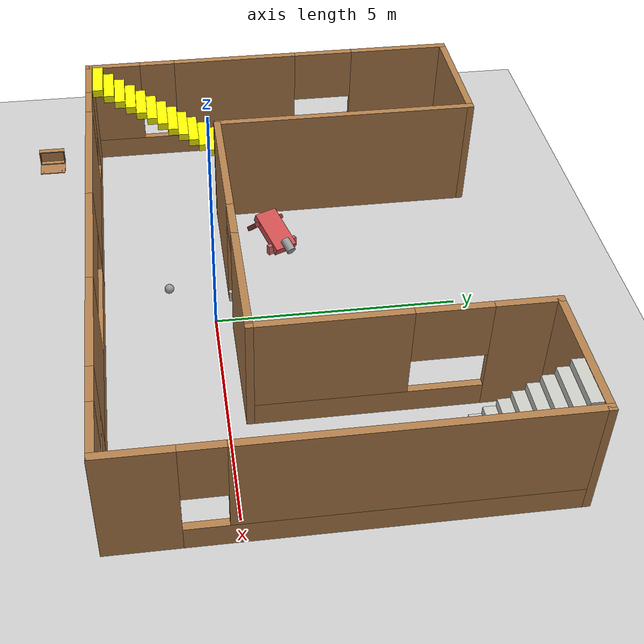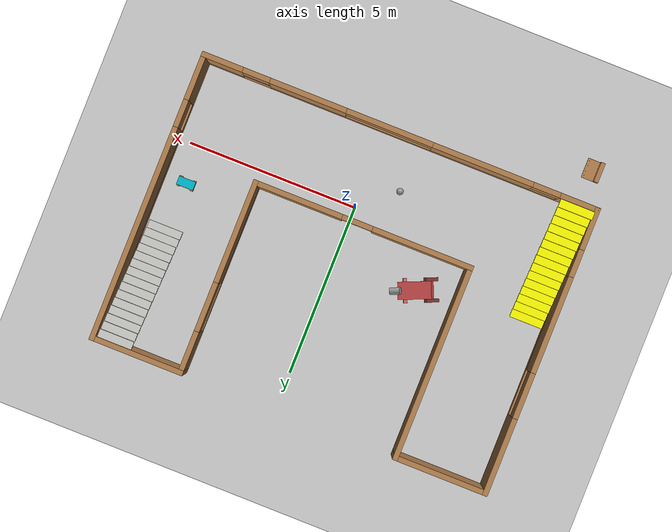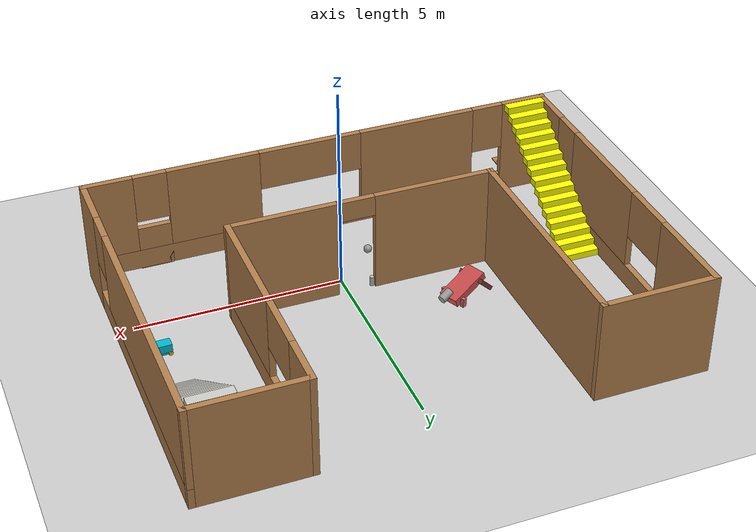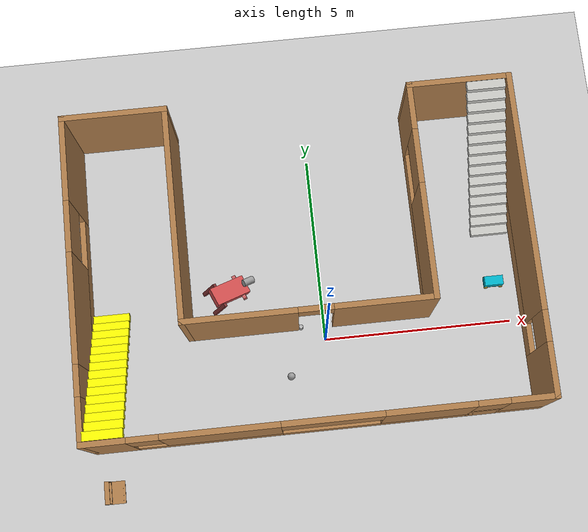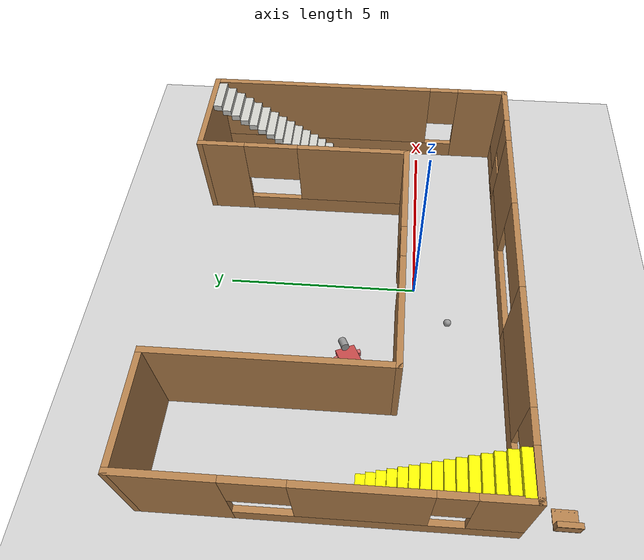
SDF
<sdf version="1.6">
 <world name="default">
  <plugin name="hello" filename="libhello.so"/>
  <light name="sun" type="directional">
   <pose>0 0 10 0 -0 0</pose>
   <diffuse>0.8 0.8 0.8 1</diffuse>
   <specular>0.2 0.2 0.2 1</specular>
   <attenuation>
    <range>1000</range>
    <constant>0.9</constant>
    <linear>0.01</linear>
    <quadratic>0.001</quadratic>
   </attenuation>
   <direction>-0.5 0.1 -0.9</direction>
  </light>
  <model name="ground_plane">
   <static>1</static>
   <link name="link">
    <collision name="collision">
     <geometry><plane><normal>0 0 1</normal><size>100 100</size></plane></geometry>
     <surface><friction><ode><mu>100</mu><mu2>50</mu2></ode></friction></surface>
    </collision>
    <visual name="visual">
     <cast_shadows>0</cast_shadows>
     <geometry><plane><normal>0 0 1</normal><size>100 100</size></plane></geometry>
     <material>
      <script><uri>file://media/materials/scripts/gazebo.material</uri><name>Gazebo/Grey</name></script>
     </material>
    </visual>
   </link>
  </model>
  <gravity>0 0 -9.8</gravity>
  <magnetic_field>6e-06 2.3e-05 -4.2e-05</magnetic_field>
  <atmosphere type="adiabatic"/>
  <physics name="default_physics" default="0" type="ode">
   <max_step_size>0.001</max_step_size>
   <real_time_factor>1</real_time_factor>
   <real_time_update_rate>1000</real_time_update_rate>
  </physics>
  <scene><ambient>0.4 0.4 0.4 1</ambient><background>0.7 0.7 0.7 1</background><shadows>1</shadows></scene>
  <spherical_coordinates>
   <surface_model>EARTH_WGS84</surface_model>
   <latitude_deg>0</latitude_deg>
   <longitude_deg>0</longitude_deg>
   <elevation>0</elevation>
   <heading_deg>0</heading_deg>
  </spherical_coordinates>
  <model name="building0">
   <pose>-0.424502 1.82994 0 0 -0 0</pose>
   <link name="Stairs_0">
    <visual name="Stairs_0_Visual_0">
     <pose>5.18201 0.711332 0.083333 0 -0 -3.14159</pose>
     <geometry><box><size>1 0.233333 0.166667</size></box></geometry>
     <material>
      <script><uri>file://media/materials/scripts/gazebo.material</uri><name>Gazebo/CeilingTiled</name></script>
      <ambient>1 0 1 1</ambient>
     </material>
     <meta><layer>0</layer></meta>
    </visual>
    <collision name="Stairs_0_Collision_0">
     <geometry><box><size>1 0.233333 0.166667</size></box></geometry>
     <pose>5.18201 0.711332 0.083333 0 -0 -3.14159</pose>
    </collision>
    <visual name="Stairs_0_Visual_1">
     <pose>5.18201 0.944665 0.25 0 -0 -3.14159</pose>
     <geometry><box><size>1 0.233333 0.166667</size></box></geometry>
     <material>
      <script><uri>file://media/materials/scripts/gazebo.material</uri><name>Gazebo/CeilingTiled</name></script>
      <ambient>1 0 1 1</ambient>
     </material>
     <meta><layer>0</layer></meta>
    </visual>
    <collision name="Stairs_0_Collision_1">
     <geometry><box><size>1 0.233333 0.166667</size></box></geometry>
     <pose>5.18201 0.944665 0.25 0 -0 -3.14159</pose>
    </collision>
    <visual name="Stairs_0_Visual_2">
     <pose>5.18201 1.178 0.416667 0 -0 -3.14159</pose>
     <geometry><box><size>1 0.233333 0.166667</size></box></geometry>
     <material>
      <script><uri>file://media/materials/scripts/gazebo.material</uri><name>Gazebo/CeilingTiled</name></script>
      <ambient>1 0 1 1</ambient>
     </material>
     <meta><layer>0</layer></meta>
    </visual>
    <collision name="Stairs_0_Collision_2">
     <geometry><box><size>1 0.233333 0.166667</size></box></geometry>
     <pose>5.18201 1.178 0.416667 0 -0 -3.14159</pose>
    </collision>
    <visual name="Stairs_0_Visual_3">
     <pose>5.18201 1.41133 0.583333 0 -0 -3.14159</pose>
     <geometry><box><size>1 0.233333 0.166667</size></box></geometry>
     <material>
      <script><uri>file://media/materials/scripts/gazebo.material</uri><name>Gazebo/CeilingTiled</name></script>
      <ambient>1 0 1 1</ambient>
     </material>
     <meta><layer>0</layer></meta>
    </visual>
    <collision name="Stairs_0_Collision_3">
     <geometry><box><size>1 0.233333 0.166667</size></box></geometry>
     <pose>5.18201 1.41133 0.583333 0 -0 -3.14159</pose>
    </collision>
    <visual name="Stairs_0_Visual_4">
     <pose>5.18201 1.64467 0.75 0 -0 -3.14159</pose>
     <geometry><box><size>1 0.233333 0.166667</size></box></geometry>
     <material>
      <script><uri>file://media/materials/scripts/gazebo.material</uri><name>Gazebo/CeilingTiled</name></script>
      <ambient>1 0 1 1</ambient>
     </material>
     <meta><layer>0</layer></meta>
    </visual>
    <collision name="Stairs_0_Collision_4">
     <geometry><box><size>1 0.233333 0.166667</size></box></geometry>
     <pose>5.18201 1.64467 0.75 0 -0 -3.14159</pose>
    </collision>
    <visual name="Stairs_0_Visual_5">
     <pose>5.18201 1.878 0.916667 0 -0 -3.14159</pose>
     <geometry><box><size>1 0.233333 0.166667</size></box></geometry>
     <material>
      <script><uri>file://media/materials/scripts/gazebo.material</uri><name>Gazebo/CeilingTiled</name></script>
      <ambient>1 0 1 1</ambient>
     </material>
     <meta><layer>0</layer></meta>
    </visual>
    <collision name="Stairs_0_Collision_5">
     <geometry><box><size>1 0.233333 0.166667</size></box></geometry>
     <pose>5.18201 1.878 0.916667 0 -0 -3.14159</pose>
    </collision>
    <visual name="Stairs_0_Visual_6">
     <pose>5.18201 2.11133 1.08333 0 -0 -3.14159</pose>
     <geometry><box><size>1 0.233333 0.166667</size></box></geometry>
     <material>
      <script><uri>file://media/materials/scripts/gazebo.material</uri><name>Gazebo/CeilingTiled</name></script>
      <ambient>1 0 1 1</ambient>
     </material>
     <meta><layer>0</layer></meta>
    </visual>
    <collision name="Stairs_0_Collision_6">
     <geometry><box><size>1 0.233333 0.166667</size></box></geometry>
     <pose>5.18201 2.11133 1.08333 0 -0 -3.14159</pose>
    </collision>
    <visual name="Stairs_0_Visual_7">
     <pose>5.18201 2.34466 1.25 0 -0 -3.14159</pose>
     <geometry><box><size>1 0.233333 0.166667</size></box></geometry>
     <material>
      <script><uri>file://media/materials/scripts/gazebo.material</uri><name>Gazebo/CeilingTiled</name></script>
      <ambient>1 0 1 1</ambient>
     </material>
     <meta><layer>0</layer></meta>
    </visual>
    <collision name="Stairs_0_Collision_7">
     <geometry><box><size>1 0.233333 0.166667</size></box></geometry>
     <pose>5.18201 2.34466 1.25 0 -0 -3.14159</pose>
    </collision>
    <visual name="Stairs_0_Visual_8">
     <pose>5.18201 2.578 1.41667 0 -0 -3.14159</pose>
     <geometry><box><size>1 0.233333 0.166667</size></box></geometry>
     <material>
      <script><uri>file://media/materials/scripts/gazebo.material</uri><name>Gazebo/CeilingTiled</name></script>
      <ambient>1 0 1 1</ambient>
     </material>
     <meta><layer>0</layer></meta>
    </visual>
    <collision name="Stairs_0_Collision_8">
     <geometry><box><size>1 0.233333 0.166667</size></box></geometry>
     <pose>5.18201 2.578 1.41667 0 -0 -3.14159</pose>
    </collision>
    <visual name="Stairs_0_Visual_9">
     <pose>5.18201 2.81133 1.58333 0 -0 -3.14159</pose>
     <geometry><box><size>1 0.233333 0.166667</size></box></geometry>
     <material>
      <script><uri>file://media/materials/scripts/gazebo.material</uri><name>Gazebo/CeilingTiled</name></script>
      <ambient>1 0 1 1</ambient>
     </material>
     <meta><layer>0</layer></meta>
    </visual>
    <collision name="Stairs_0_Collision_9">
     <geometry><box><size>1 0.233333 0.166667</size></box></geometry>
     <pose>5.18201 2.81133 1.58333 0 -0 -3.14159</pose>
    </collision>
    <visual name="Stairs_0_Visual_10">
     <pose>5.18201 3.04467 1.75 0 -0 -3.14159</pose>
     <geometry><box><size>1 0.233333 0.166667</size></box></geometry>
     <material>
      <script><uri>file://media/materials/scripts/gazebo.material</uri><name>Gazebo/CeilingTiled</name></script>
      <ambient>1 0 1 1</ambient>
     </material>
     <meta><layer>0</layer></meta>
    </visual>
    <collision name="Stairs_0_Collision_10">
     <geometry><box><size>1 0.233333 0.166667</size></box></geometry>
     <pose>5.18201 3.04467 1.75 0 -0 -3.14159</pose>
    </collision>
    <visual name="Stairs_0_Visual_11">
     <pose>5.18201 3.278 1.91667 0 -0 -3.14159</pose>
     <geometry><box><size>1 0.233333 0.166667</size></box></geometry>
     <material>
      <script><uri>file://media/materials/scripts/gazebo.material</uri><name>Gazebo/CeilingTiled</name></script>
      <ambient>1 0 1 1</ambient>
     </material>
     <meta><layer>0</layer></meta>
    </visual>
    <collision name="Stairs_0_Collision_11">
     <geometry><box><size>1 0.233333 0.166667</size></box></geometry>
     <pose>5.18201 3.278 1.91667 0 -0 -3.14159</pose>
    </collision>
    <visual name="Stairs_0_Visual_12">
     <pose>5.18201 3.51133 2.08333 0 -0 -3.14159</pose>
     <geometry><box><size>1 0.233333 0.166667</size></box></geometry>
     <material>
      <script><uri>file://media/materials/scripts/gazebo.material</uri><name>Gazebo/CeilingTiled</name></script>
      <ambient>1 0 1 1</ambient>
     </material>
     <meta><layer>0</layer></meta>
    </visual>
    <collision name="Stairs_0_Collision_12">
     <geometry><box><size>1 0.233333 0.166667</size></box></geometry>
     <pose>5.18201 3.51133 2.08333 0 -0 -3.14159</pose>
    </collision>
    <visual name="Stairs_0_Visual_13">
     <pose>5.18201 3.74466 2.25 0 -0 -3.14159</pose>
     <geometry><box><size>1 0.233333 0.166667</size></box></geometry>
     <material>
      <script><uri>file://media/materials/scripts/gazebo.material</uri><name>Gazebo/CeilingTiled</name></script>
      <ambient>1 0 1 1</ambient>
     </material>
     <meta><layer>0</layer></meta>
    </visual>
    <collision name="Stairs_0_Collision_13">
     <geometry><box><size>1 0.233333 0.166667</size></box></geometry>
     <pose>5.18201 3.74466 2.25 0 -0 -3.14159</pose>
    </collision>
    <visual name="Stairs_0_Visual_14">
     <pose>5.18201 3.978 2.41667 0 -0 -3.14159</pose>
     <geometry><box><size>1 0.233333 0.166667</size></box></geometry>
     <material>
      <script><uri>file://media/materials/scripts/gazebo.material</uri><name>Gazebo/CeilingTiled</name></script>
      <ambient>1 0 1 1</ambient>
     </material>
     <meta><layer>0</layer></meta>
    </visual>
    <collision name="Stairs_0_Collision_14">
     <geometry><box><size>1 0.233333 0.166667</size></box></geometry>
     <pose>5.18201 3.978 2.41667 0 -0 -3.14159</pose>
    </collision>
   </link>
   <link name="Stairs_1">
    <visual name="Stairs_1_Visual_0">
     <pose>-5.25693 -0.708464 0.083333 0 -0 0</pose>
     <geometry><box><size>1 0.233333 0.166667</size></box></geometry>
     <material>
      <script><uri>file://media/materials/scripts/gazebo.material</uri><name>Gazebo/Grey</name></script>
      <ambient>1 1 0 1</ambient>
     </material>
     <meta><layer>0</layer></meta>
    </visual>
    <collision name="Stairs_1_Collision_0">
     <geometry><box><size>1 0.233333 0.166667</size></box></geometry>
     <pose>-5.25693 -0.708464 0.083333 0 -0 0</pose>
    </collision>
    <visual name="Stairs_1_Visual_1">
     <pose>-5.25693 -0.941797 0.25 0 -0 0</pose>
     <geometry><box><size>1 0.233333 0.166667</size></box></geometry>
     <material>
      <script><uri>file://media/materials/scripts/gazebo.material</uri><name>Gazebo/Grey</name></script>
      <ambient>1 1 0 1</ambient>
     </material>
     <meta><layer>0</layer></meta>
    </visual>
    <collision name="Stairs_1_Collision_1">
     <geometry><box><size>1 0.233333 0.166667</size></box></geometry>
     <pose>-5.25693 -0.941797 0.25 0 -0 0</pose>
    </collision>
    <visual name="Stairs_1_Visual_2">
     <pose>-5.25693 -1.17513 0.416667 0 -0 0</pose>
     <geometry><box><size>1 0.233333 0.166667</size></box></geometry>
     <material>
      <script><uri>file://media/materials/scripts/gazebo.material</uri><name>Gazebo/Grey</name></script>
      <ambient>1 1 0 1</ambient>
     </material>
     <meta><layer>0</layer></meta>
    </visual>
    <collision name="Stairs_1_Collision_2">
     <geometry><box><size>1 0.233333 0.166667</size></box></geometry>
     <pose>-5.25693 -1.17513 0.416667 0 -0 0</pose>
    </collision>
    <visual name="Stairs_1_Visual_3">
     <pose>-5.25693 -1.40846 0.583333 0 -0 0</pose>
     <geometry><box><size>1 0.233333 0.166667</size></box></geometry>
     <material>
      <script><uri>file://media/materials/scripts/gazebo.material</uri><name>Gazebo/Grey</name></script>
      <ambient>1 1 0 1</ambient>
     </material>
     <meta><layer>0</layer></meta>
    </visual>
    <collision name="Stairs_1_Collision_3">
     <geometry><box><size>1 0.233333 0.166667</size></box></geometry>
     <pose>-5.25693 -1.40846 0.583333 0 -0 0</pose>
    </collision>
    <visual name="Stairs_1_Visual_4">
     <pose>-5.25693 -1.6418 0.75 0 -0 0</pose>
     <geometry><box><size>1 0.233333 0.166667</size></box></geometry>
     <material>
      <script><uri>file://media/materials/scripts/gazebo.material</uri><name>Gazebo/Grey</name></script>
      <ambient>1 1 0 1</ambient>
     </material>
     <meta><layer>0</layer></meta>
    </visual>
    <collision name="Stairs_1_Collision_4">
     <geometry><box><size>1 0.233333 0.166667</size></box></geometry>
     <pose>-5.25693 -1.6418 0.75 0 -0 0</pose>
    </collision>
    <visual name="Stairs_1_Visual_5">
     <pose>-5.25693 -1.87513 0.916667 0 -0 0</pose>
     <geometry><box><size>1 0.233333 0.166667</size></box></geometry>
     <material>
      <script><uri>file://media/materials/scripts/gazebo.material</uri><name>Gazebo/Grey</name></script>
      <ambient>1 1 0 1</ambient>
     </material>
     <meta><layer>0</layer></meta>
    </visual>
    <collision name="Stairs_1_Collision_5">
     <geometry><box><size>1 0.233333 0.166667</size></box></geometry>
     <pose>-5.25693 -1.87513 0.916667 0 -0 0</pose>
    </collision>
    <visual name="Stairs_1_Visual_6">
     <pose>-5.25693 -2.10846 1.08333 0 -0 0</pose>
     <geometry><box><size>1 0.233333 0.166667</size></box></geometry>
     <material>
      <script><uri>file://media/materials/scripts/gazebo.material</uri><name>Gazebo/Grey</name></script>
      <ambient>1 1 0 1</ambient>
     </material>
     <meta><layer>0</layer></meta>
    </visual>
    <collision name="Stairs_1_Collision_6">
     <geometry><box><size>1 0.233333 0.166667</size></box></geometry>
     <pose>-5.25693 -2.10846 1.08333 0 -0 0</pose>
    </collision>
    <visual name="Stairs_1_Visual_7">
     <pose>-5.25693 -2.3418 1.25 0 -0 0</pose>
     <geometry><box><size>1 0.233333 0.166667</size></box></geometry>
     <material>
      <script><uri>file://media/materials/scripts/gazebo.material</uri><name>Gazebo/Grey</name></script>
      <ambient>1 1 0 1</ambient>
     </material>
     <meta><layer>0</layer></meta>
    </visual>
    <collision name="Stairs_1_Collision_7">
     <geometry><box><size>1 0.233333 0.166667</size></box></geometry>
     <pose>-5.25693 -2.3418 1.25 0 -0 0</pose>
    </collision>
    <visual name="Stairs_1_Visual_8">
     <pose>-5.25693 -2.57513 1.41667 0 -0 0</pose>
     <geometry><box><size>1 0.233333 0.166667</size></box></geometry>
     <material>
      <script><uri>file://media/materials/scripts/gazebo.material</uri><name>Gazebo/Grey</name></script>
      <ambient>1 1 0 1</ambient>
     </material>
     <meta><layer>0</layer></meta>
    </visual>
    <collision name="Stairs_1_Collision_8">
     <geometry><box><size>1 0.233333 0.166667</size></box></geometry>
     <pose>-5.25693 -2.57513 1.41667 0 -0 0</pose>
    </collision>
    <visual name="Stairs_1_Visual_9">
     <pose>-5.25693 -2.80846 1.58333 0 -0 0</pose>
     <geometry><box><size>1 0.233333 0.166667</size></box></geometry>
     <material>
      <script><uri>file://media/materials/scripts/gazebo.material</uri><name>Gazebo/Grey</name></script>
      <ambient>1 1 0 1</ambient>
     </material>
     <meta><layer>0</layer></meta>
    </visual>
    <collision name="Stairs_1_Collision_9">
     <geometry><box><size>1 0.233333 0.166667</size></box></geometry>
     <pose>-5.25693 -2.80846 1.58333 0 -0 0</pose>
    </collision>
    <visual name="Stairs_1_Visual_10">
     <pose>-5.25693 -3.0418 1.75 0 -0 0</pose>
     <geometry><box><size>1 0.233333 0.166667</size></box></geometry>
     <material>
      <script><uri>file://media/materials/scripts/gazebo.material</uri><name>Gazebo/Grey</name></script>
      <ambient>1 1 0 1</ambient>
     </material>
     <meta><layer>0</layer></meta>
    </visual>
    <collision name="Stairs_1_Collision_10">
     <geometry><box><size>1 0.233333 0.166667</size></box></geometry>
     <pose>-5.25693 -3.0418 1.75 0 -0 0</pose>
    </collision>
    <visual name="Stairs_1_Visual_11">
     <pose>-5.25693 -3.27513 1.91667 0 -0 0</pose>
     <geometry><box><size>1 0.233333 0.166667</size></box></geometry>
     <material>
      <script><uri>file://media/materials/scripts/gazebo.material</uri><name>Gazebo/Grey</name></script>
      <ambient>1 1 0 1</ambient>
     </material>
     <meta><layer>0</layer></meta>
    </visual>
    <collision name="Stairs_1_Collision_11">
     <geometry><box><size>1 0.233333 0.166667</size></box></geometry>
     <pose>-5.25693 -3.27513 1.91667 0 -0 0</pose>
    </collision>
    <visual name="Stairs_1_Visual_12">
     <pose>-5.25693 -3.50846 2.08333 0 -0 0</pose>
     <geometry><box><size>1 0.233333 0.166667</size></box></geometry>
     <material>
      <script><uri>file://media/materials/scripts/gazebo.material</uri><name>Gazebo/Grey</name></script>
      <ambient>1 1 0 1</ambient>
     </material>
     <meta><layer>0</layer></meta>
    </visual>
    <collision name="Stairs_1_Collision_12">
     <geometry><box><size>1 0.233333 0.166667</size></box></geometry>
     <pose>-5.25693 -3.50846 2.08333 0 -0 0</pose>
    </collision>
    <visual name="Stairs_1_Visual_13">
     <pose>-5.25693 -3.7418 2.25 0 -0 0</pose>
     <geometry><box><size>1 0.233333 0.166667</size></box></geometry>
     <material>
      <script><uri>file://media/materials/scripts/gazebo.material</uri><name>Gazebo/Grey</name></script>
      <ambient>1 1 0 1</ambient>
     </material>
     <meta><layer>0</layer></meta>
    </visual>
    <collision name="Stairs_1_Collision_13">
     <geometry><box><size>1 0.233333 0.166667</size></box></geometry>
     <pose>-5.25693 -3.7418 2.25 0 -0 0</pose>
    </collision>
    <visual name="Stairs_1_Visual_14">
     <pose>-5.25693 -3.97513 2.41667 0 -0 0</pose>
     <geometry><box><size>1 0.233333 0.166667</size></box></geometry>
     <material>
      <script><uri>file://media/materials/scripts/gazebo.material</uri><name>Gazebo/Grey</name></script>
      <ambient>1 1 0 1</ambient>
     </material>
     <meta><layer>0</layer></meta>
    </visual>
    <collision name="Stairs_1_Collision_14">
     <geometry><box><size>1 0.233333 0.166667</size></box></geometry>
     <pose>-5.25693 -3.97513 2.41667 0 -0 0</pose>
    </collision>
   </link>
   <link name="Wall_29">
    <pose>-5.8 0 0 0 0 -1.5708</pose>
    <visual name="Wall_29_Visual_0">
     <pose>-3.11517 0 1.25 0 -0 0</pose>
     <geometry><box><size>2.26965 0.15 2.5</size></box></geometry>
     <material>
      <script><uri>file://media/materials/scripts/gazebo.material</uri><name>Gazebo/Wood</name></script>
      <ambient>1 0.764706 0.305882 1</ambient>
     </material>
     <meta><layer>0</layer></meta>
    </visual>
    <collision name="Wall_29_Collision_0">
     <geometry><box><size>2.26965 0.15 2.5</size></box></geometry>
     <pose>-3.11517 0 1.25 0 -0 0</pose>
    </collision>
    <visual name="Wall_29_Visual_1">
     <pose>1.13482 0 0.25 0 -0 0</pose>
     <geometry><box><size>6.23035 0.15 0.5</size></box></geometry>
     <material>
      <script><uri>file://media/materials/scripts/gazebo.material</uri><name>Gazebo/Wood</name></script>
      <ambient>1 0.764706 0.305882 1</ambient>
     </material>
     <meta><layer>0</layer></meta>
    </visual>
    <collision name="Wall_29_Collision_1">
     <geometry><box><size>6.23035 0.15 0.5</size></box></geometry>
     <pose>1.13482 0 0.25 0 -0 0</pose>
    </collision>
    <visual name="Wall_29_Visual_2">
     <pose>0.782995 0 1.5 0 -0 0</pose>
     <geometry><box><size>2.84056 0.15 2</size></box></geometry>
     <material>
      <script><uri>file://media/materials/scripts/gazebo.material</uri><name>Gazebo/Wood</name></script>
      <ambient>1 0.764706 0.305882 1</ambient>
     </material>
     <meta><layer>0</layer></meta>
    </visual>
    <collision name="Wall_29_Collision_2">
     <geometry><box><size>2.84056 0.15 2</size></box></geometry>
     <pose>0.782995 0 1.5 0 -0 0</pose>
    </collision>
    <visual name="Wall_29_Visual_3">
     <pose>3.62664 0 1.5 0 -0 0</pose>
     <geometry><box><size>1.24673 0.15 2</size></box></geometry>
     <material>
      <script><uri>file://media/materials/scripts/gazebo.material</uri><name>Gazebo/Wood</name></script>
      <ambient>1 0.764706 0.305882 1</ambient>
     </material>
     <meta><layer>0</layer></meta>
    </visual>
    <collision name="Wall_29_Collision_3">
     <geometry><box><size>1.24673 0.15 2</size></box></geometry>
     <pose>3.62664 0 1.5 0 -0 0</pose>
    </collision>
    <visual name="Wall_29_Visual_4">
     <pose>-1.30882 0 1.9 0 -0 0</pose>
     <geometry><box><size>1.34307 0.15 1.2</size></box></geometry>
     <material>
      <script><uri>file://media/materials/scripts/gazebo.material</uri><name>Gazebo/Wood</name></script>
      <ambient>1 0.764706 0.305882 1</ambient>
     </material>
     <meta><layer>0</layer></meta>
    </visual>
    <collision name="Wall_29_Collision_4">
     <geometry><box><size>1.34307 0.15 1.2</size></box></geometry>
     <pose>-1.30882 0 1.9 0 -0 0</pose>
    </collision>
    <visual name="Wall_29_Visual_5">
     <pose>2.60327 0 1.9 0 -0 0</pose>
     <geometry><box><size>0.8 0.15 1.2</size></box></geometry>
     <material>
      <script><uri>file://media/materials/scripts/gazebo.material</uri><name>Gazebo/Wood</name></script>
      <ambient>1 0.764706 0.305882 1</ambient>
     </material>
     <meta><layer>0</layer></meta>
    </visual>
    <collision name="Wall_29_Collision_5">
     <geometry><box><size>0.8 0.15 1.2</size></box></geometry>
     <pose>2.60327 0 1.9 0 -0 0</pose>
    </collision>
   </link>
   <link name="Wall_30">
    <pose>0 -4.175 0 0 -0 0</pose>
    <visual name="Wall_30_Visual_0">
     <pose>-5.2933 0 1.25 0 -0 0</pose>
     <geometry><box><size>1.1634 0.15 2.5</size></box></geometry>
     <material>
      <script><uri>file://media/materials/scripts/gazebo.material</uri><name>Gazebo/Wood</name></script>
      <ambient>1 0.764706 0.305882 1</ambient>
     </material>
     <meta><layer>0</layer></meta>
    </visual>
    <collision name="Wall_30_Collision_0">
     <geometry><box><size>1.1634 0.15 2.5</size></box></geometry>
     <pose>-5.2933 0 1.25 0 -0 0</pose>
    </collision>
    <visual name="Wall_30_Visual_1">
     <pose>-2.83101 0 0.25 0 -0 0</pose>
     <geometry><box><size>3.76118 0.15 0.5</size></box></geometry>
     <material>
      <script><uri>file://media/materials/scripts/gazebo.material</uri><name>Gazebo/Wood</name></script>
      <ambient>1 0.764706 0.305882 1</ambient>
     </material>
     <meta><layer>0</layer></meta>
    </visual>
    <collision name="Wall_30_Collision_1">
     <geometry><box><size>3.76118 0.15 0.5</size></box></geometry>
     <pose>-2.83101 0 0.25 0 -0 0</pose>
    </collision>
    <visual name="Wall_30_Visual_2">
     <pose>2.46229 0 0.25 0 -0 0</pose>
     <geometry><box><size>6.82542 0.15 0.5</size></box></geometry>
     <material>
      <script><uri>file://media/materials/scripts/gazebo.material</uri><name>Gazebo/Wood</name></script>
      <ambient>1 0.764706 0.305882 1</ambient>
     </material>
     <meta><layer>0</layer></meta>
    </visual>
    <collision name="Wall_30_Collision_2">
     <geometry><box><size>6.82542 0.15 0.5</size></box></geometry>
     <pose>2.46229 0 0.25 0 -0 0</pose>
    </collision>
    <visual name="Wall_30_Visual_3">
     <pose>2.72818 0 1.5 0 -0 0</pose>
     <geometry><box><size>2.2572 0.15 2</size></box></geometry>
     <material>
      <script><uri>file://media/materials/scripts/gazebo.material</uri><name>Gazebo/Wood</name></script>
      <ambient>1 0.764706 0.305882 1</ambient>
     </material>
     <meta><layer>0</layer></meta>
    </visual>
    <collision name="Wall_30_Collision_3">
     <geometry><box><size>2.2572 0.15 2</size></box></geometry>
     <pose>2.72818 0 1.5 0 -0 0</pose>
    </collision>
    <visual name="Wall_30_Visual_4">
     <pose>5.26589 0 1.5 0 -0 0</pose>
     <geometry><box><size>1.21821 0.15 2</size></box></geometry>
     <material>
      <script><uri>file://media/materials/scripts/gazebo.material</uri><name>Gazebo/Wood</name></script>
      <ambient>1 0.764706 0.305882 1</ambient>
     </material>
     <meta><layer>0</layer></meta>
    </visual>
    <collision name="Wall_30_Collision_4">
     <geometry><box><size>1.21821 0.15 2</size></box></geometry>
     <pose>5.26589 0 1.5 0 -0 0</pose>
    </collision>
    <visual name="Wall_30_Visual_5">
     <pose>4.25679 0 0.5 0 -0 0</pose>
     <geometry><box><size>0.8 0.15 1.2</size></box></geometry>
     <material>
      <script><uri>file://media/materials/scripts/gazebo.material</uri><name>Gazebo/Wood</name></script>
      <ambient>1 0.764706 0.305882 1</ambient>
     </material>
     <meta><layer>0</layer></meta>
    </visual>
    <collision name="Wall_30_Collision_5">
     <geometry><box><size>0.8 0.15 1.2</size></box></geometry>
     <pose>4.25679 0 0.5 0 -0 0</pose>
    </collision>
    <visual name="Wall_30_Visual_6">
     <pose>-2.43101 0 1.5 0 -0 0</pose>
     <geometry><box><size>2.96118 0.15 2</size></box></geometry>
     <material>
      <script><uri>file://media/materials/scripts/gazebo.material</uri><name>Gazebo/Wood</name></script>
      <ambient>1 0.764706 0.305882 1</ambient>
     </material>
     <meta><layer>0</layer></meta>
    </visual>
    <collision name="Wall_30_Collision_6">
     <geometry><box><size>2.96118 0.15 2</size></box></geometry>
     <pose>-2.43101 0 1.5 0 -0 0</pose>
    </collision>
    <visual name="Wall_30_Visual_7">
     <pose>-2.43101 0 1.5 0 -0 0</pose>
     <geometry><box><size>2.96118 0.15 2</size></box></geometry>
     <material>
      <script><uri>file://media/materials/scripts/gazebo.material</uri><name>Gazebo/Wood</name></script>
      <ambient>1 0.764706 0.305882 1</ambient>
     </material>
     <meta><layer>0</layer></meta>
    </visual>
    <collision name="Wall_30_Collision_7">
     <geometry><box><size>2.96118 0.15 2</size></box></geometry>
     <pose>-2.43101 0 1.5 0 -0 0</pose>
    </collision>
    <visual name="Wall_30_Visual_8">
     <pose>-4.3116 0 1.9 0 -0 0</pose>
     <geometry><box><size>0.8 0.15 1.2</size></box></geometry>
     <material>
      <script><uri>file://media/materials/scripts/gazebo.material</uri><name>Gazebo/Wood</name></script>
      <ambient>1 0.764706 0.305882 1</ambient>
     </material>
     <meta><layer>0</layer></meta>
    </visual>
    <collision name="Wall_30_Collision_8">
     <geometry><box><size>0.8 0.15 1.2</size></box></geometry>
     <pose>-4.3116 0 1.9 0 -0 0</pose>
    </collision>
    <visual name="Wall_30_Visual_9">
     <pose>4.25679 0 1.9 0 -0 0</pose>
     <geometry><box><size>0.8 0.15 1.2</size></box></geometry>
     <material>
      <script><uri>file://media/materials/scripts/gazebo.material</uri><name>Gazebo/Wood</name></script>
      <ambient>1 0.764706 0.305882 1</ambient>
     </material>
     <meta><layer>0</layer></meta>
    </visual>
    <collision name="Wall_30_Collision_9">
     <geometry><box><size>0.8 0.15 1.2</size></box></geometry>
     <pose>4.25679 0 1.9 0 -0 0</pose>
    </collision>
    <visual name="Wall_30_Visual_10">
     <pose>0.324583 0 2 0 -0 0</pose>
     <geometry><box><size>2.55 0.15 1</size></box></geometry>
     <material>
      <script><uri>file://media/materials/scripts/gazebo.material</uri><name>Gazebo/Wood</name></script>
      <ambient>1 0.764706 0.305882 1</ambient>
     </material>
     <meta><layer>0</layer></meta>
    </visual>
    <collision name="Wall_30_Collision_10">
     <geometry><box><size>2.55 0.15 1</size></box></geometry>
     <pose>0.324583 0 2 0 -0 0</pose>
    </collision>
    <visual name="Wall_30_Visual_11">
     <pose>0.324583 0 2 0 -0 0</pose>
     <geometry><box><size>2.55 0.15 1</size></box></geometry>
     <material>
      <script><uri>file://media/materials/scripts/gazebo.material</uri><name>Gazebo/Wood</name></script>
      <ambient>1 0.764706 0.305882 1</ambient>
     </material>
     <meta><layer>0</layer></meta>
    </visual>
    <collision name="Wall_30_Collision_11">
     <geometry><box><size>2.55 0.15 1</size></box></geometry>
     <pose>0.324583 0 2 0 -0 0</pose>
    </collision>
   </link>
   <link name="Wall_31">
    <pose>5.8 0 0 0 -0 1.5708</pose>
    <visual name="Wall_31_Visual_0">
     <pose>-3.54618 0 1.25 0 -0 0</pose>
     <geometry><box><size>1.40763 0.15 2.5</size></box></geometry>
     <material>
      <script><uri>file://media/materials/scripts/gazebo.material</uri><name>Gazebo/Wood</name></script>
      <ambient>1 0.764706 0.305882 1</ambient>
     </material>
     <meta><layer>0</layer></meta>
    </visual>
    <collision name="Wall_31_Collision_0">
     <geometry><box><size>1.40763 0.15 2.5</size></box></geometry>
     <pose>-3.54618 0 1.25 0 -0 0</pose>
    </collision>
    <visual name="Wall_31_Visual_1">
     <pose>0.703818 0 0.25 0 -0 0</pose>
     <geometry><box><size>7.09237 0.15 0.5</size></box></geometry>
     <material>
      <script><uri>file://media/materials/scripts/gazebo.material</uri><name>Gazebo/Wood</name></script>
      <ambient>1 0.764706 0.305882 1</ambient>
     </material>
     <meta><layer>0</layer></meta>
    </visual>
    <collision name="Wall_31_Collision_1">
     <geometry><box><size>7.09237 0.15 0.5</size></box></geometry>
     <pose>0.703818 0 0.25 0 -0 0</pose>
    </collision>
    <visual name="Wall_31_Visual_2">
     <pose>1.10382 0 1.5 0 -0 0</pose>
     <geometry><box><size>6.29237 0.15 2</size></box></geometry>
     <material>
      <script><uri>file://media/materials/scripts/gazebo.material</uri><name>Gazebo/Wood</name></script>
      <ambient>1 0.764706 0.305882 1</ambient>
     </material>
     <meta><layer>0</layer></meta>
    </visual>
    <collision name="Wall_31_Collision_2">
     <geometry><box><size>6.29237 0.15 2</size></box></geometry>
     <pose>1.10382 0 1.5 0 -0 0</pose>
    </collision>
    <visual name="Wall_31_Visual_3">
     <pose>-2.44237 0 1.9 0 -0 0</pose>
     <geometry><box><size>0.8 0.15 1.2</size></box></geometry>
     <material>
      <script><uri>file://media/materials/scripts/gazebo.material</uri><name>Gazebo/Wood</name></script>
      <ambient>1 0.764706 0.305882 1</ambient>
     </material>
     <meta><layer>0</layer></meta>
    </visual>
    <collision name="Wall_31_Collision_3">
     <geometry><box><size>0.8 0.15 1.2</size></box></geometry>
     <pose>-2.44237 0 1.9 0 -0 0</pose>
    </collision>
   </link>
   <link name="Wall_32">
    <collision name="Wall_32_Collision">
     <geometry><box><size>2.75 0.15 2.5</size></box></geometry>
     <pose>0 0 1.25 0 -0 0</pose>
    </collision>
    <visual name="Wall_32_Visual">
     <pose>0 0 1.25 0 -0 0</pose>
     <geometry><box><size>2.75 0.15 2.5</size></box></geometry>
     <material>
      <script><uri>file://media/materials/scripts/gazebo.material</uri><name>Gazebo/Wood</name></script>
      <ambient>1 0.764706 0.305882 1</ambient>
     </material>
     <meta><layer>0</layer></meta>
    </visual>
    <pose>4.5 4.175 0 0 -0 3.14159</pose>
   </link>
   <link name="Wall_33">
    <pose>3.2 1.375 0 0 0 -1.5708</pose>
    <visual name="Wall_33_Visual_0">
     <pose>-2.23296 0 1.25 0 -0 0</pose>
     <geometry><box><size>1.28409 0.15 2.5</size></box></geometry>
     <material>
      <script><uri>file://media/materials/scripts/gazebo.material</uri><name>Gazebo/Wood</name></script>
      <ambient>1 0.764706 0.305882 1</ambient>
     </material>
     <meta><layer>0</layer></meta>
    </visual>
    <collision name="Wall_33_Collision_0">
     <geometry><box><size>1.28409 0.15 2.5</size></box></geometry>
     <pose>-2.23296 0 1.25 0 -0 0</pose>
    </collision>
    <visual name="Wall_33_Visual_1">
     <pose>0.642043 0 0.25 0 -0 0</pose>
     <geometry><box><size>4.46591 0.15 0.5</size></box></geometry>
     <material>
      <script><uri>file://media/materials/scripts/gazebo.material</uri><name>Gazebo/Wood</name></script>
      <ambient>1 0.764706 0.305882 1</ambient>
     </material>
     <meta><layer>0</layer></meta>
    </visual>
    <collision name="Wall_33_Collision_1">
     <geometry><box><size>4.46591 0.15 0.5</size></box></geometry>
     <pose>0.642043 0 0.25 0 -0 0</pose>
    </collision>
    <visual name="Wall_33_Visual_2">
     <pose>1.36386 0 1.5 0 -0 0</pose>
     <geometry><box><size>3.02228 0.15 2</size></box></geometry>
     <material>
      <script><uri>file://media/materials/scripts/gazebo.material</uri><name>Gazebo/Wood</name></script>
      <ambient>1 0.764706 0.305882 1</ambient>
     </material>
     <meta><layer>0</layer></meta>
    </visual>
    <collision name="Wall_33_Collision_2">
     <geometry><box><size>3.02228 0.15 2</size></box></geometry>
     <pose>1.36386 0 1.5 0 -0 0</pose>
    </collision>
    <visual name="Wall_33_Visual_3">
     <pose>-0.869097 0 1.9 0 -0 0</pose>
     <geometry><box><size>1.44363 0.15 1.2</size></box></geometry>
     <material>
      <script><uri>file://media/materials/scripts/gazebo.material</uri><name>Gazebo/Wood</name></script>
      <ambient>1 0.764706 0.305882 1</ambient>
     </material>
     <meta><layer>0</layer></meta>
    </visual>
    <collision name="Wall_33_Collision_3">
     <geometry><box><size>1.44363 0.15 1.2</size></box></geometry>
     <pose>-0.869097 0 1.9 0 -0 0</pose>
    </collision>
   </link>
   <link name="Wall_34">
    <pose>0.025 -1.425 0 0 -0 3.14159</pose>
    <visual name="Wall_34_Visual_0">
     <pose>-1.93442 0 1.25 0 -0 0</pose>
     <geometry><box><size>2.63116 0.15 2.5</size></box></geometry>
     <material>
      <script><uri>file://media/materials/scripts/gazebo.material</uri><name>Gazebo/Wood</name></script>
      <ambient>1 0.764706 0.305882 1</ambient>
     </material>
     <meta><layer>0</layer></meta>
    </visual>
    <collision name="Wall_34_Collision_0">
     <geometry><box><size>2.63116 0.15 2.5</size></box></geometry>
     <pose>-1.93442 0 1.25 0 -0 0</pose>
    </collision>
    <visual name="Wall_34_Visual_1">
     <pose>1.76558 0 1.25 0 -0 0</pose>
     <geometry><box><size>2.96884 0.15 2.5</size></box></geometry>
     <material>
      <script><uri>file://media/materials/scripts/gazebo.material</uri><name>Gazebo/Wood</name></script>
      <ambient>1 0.764706 0.305882 1</ambient>
     </material>
     <meta><layer>0</layer></meta>
    </visual>
    <collision name="Wall_34_Collision_1">
     <geometry><box><size>2.96884 0.15 2.5</size></box></geometry>
     <pose>1.76558 0 1.25 0 -0 0</pose>
    </collision>
    <visual name="Wall_34_Visual_2">
     <pose>-0.168844 0 2.25 0 -0 0</pose>
     <geometry><box><size>0.9 0.15 0.5</size></box></geometry>
     <material>
      <script><uri>file://media/materials/scripts/gazebo.material</uri><name>Gazebo/Wood</name></script>
      <ambient>1 0.764706 0.305882 1</ambient>
     </material>
     <meta><layer>0</layer></meta>
    </visual>
    <collision name="Wall_34_Collision_2">
     <geometry><box><size>0.9 0.15 0.5</size></box></geometry>
     <pose>-0.168844 0 2.25 0 -0 0</pose>
    </collision>
   </link>
   <link name="Wall_35">
    <collision name="Wall_35_Collision">
     <geometry><box><size>5.75 0.15 2.5</size></box></geometry>
     <pose>0 0 1.25 0 -0 0</pose>
    </collision>
    <visual name="Wall_35_Visual">
     <pose>0 0 1.25 0 -0 0</pose>
     <geometry><box><size>5.75 0.15 2.5</size></box></geometry>
     <material>
      <script><uri>file://media/materials/scripts/gazebo.material</uri><name>Gazebo/Wood</name></script>
      <ambient>1 0.764706 0.305882 1</ambient>
     </material>
     <meta><layer>0</layer></meta>
    </visual>
    <pose>-3.15 1.375 0 0 -0 1.5708</pose>
   </link>
   <link name="Wall_36">
    <collision name="Wall_36_Collision">
     <geometry><box><size>2.8 0.15 2.5</size></box></geometry>
     <pose>0 0 1.25 0 -0 0</pose>
    </collision>
    <visual name="Wall_36_Visual">
     <pose>0 0 1.25 0 -0 0</pose>
     <geometry><box><size>2.8 0.15 2.5</size></box></geometry>
     <material>
      <script><uri>file://media/materials/scripts/gazebo.material</uri><name>Gazebo/Wood</name></script>
      <ambient>1 0.764706 0.305882 1</ambient>
     </material>
     <meta><layer>0</layer></meta>
    </visual>
    <pose>-4.475 4.175 0 0 0 -3.14159</pose>
   </link>
   <static>1</static>
  </model>
  <model name="animal">
   <link name="link_2">
    <pose>-0.089432 0 0.1 0 -0 0</pose>
    <inertial>
     <mass>1</mass>
     <inertia>
      <ixx>0.166667</ixx>
      <ixy>0</ixy>
      <ixz>0</ixz>
      <iyy>0.166667</iyy>
      <iyz>0</iyz>
      <izz>0.166667</izz>
     </inertia>
    </inertial>
    <visual name="visual">
     <geometry><box><size>1 0.5 0.2</size></box></geometry>
     <material>
      <lighting>1</lighting>
      <script><uri>file://media/materials/scripts/gazebo.material</uri><name>Gazebo/Grey</name></script>
      <shader type="pixel"><normal_map>__default__</normal_map></shader>
      <ambient>0.3 0.3 0.3 1</ambient>
      <diffuse>0.8 0.3 0.3 1</diffuse>
      <specular>0.01 0.01 0.01 1</specular>
      <emissive>0 0 0 1</emissive>
     </material>
    </visual>
    <collision name="collision">
     <geometry><box><size>1 0.5 0.2</size></box></geometry>
     <surface>
      <friction>
       <ode><mu>1</mu><mu2>1</mu2><fdir1>0 0 0</fdir1><slip1>0</slip1><slip2>0</slip2></ode>
       <torsional>
        <coefficient>1</coefficient>
        <patch_radius>0</patch_radius>
        <surface_radius>0</surface_radius>
        <use_patch_radius>1</use_patch_radius>
        <ode><slip>0</slip></ode>
       </torsional>
      </friction>
      <bounce><restitution_coefficient>0</restitution_coefficient><threshold>1e+06</threshold></bounce>
      <contact>
       <collide_without_contact>0</collide_without_contact>
       <collide_without_contact_bitmask>1</collide_without_contact_bitmask>
       <collide_bitmask>1</collide_bitmask>
       <ode>
        <soft_cfm>0</soft_cfm>
        <soft_erp>0.2</soft_erp>
        <kp>1e+13</kp>
        <kd>1</kd>
        <max_vel>0.01</max_vel>
        <min_depth>0</min_depth>
       </ode>
       <bullet>
        <split_impulse>1</split_impulse>
        <split_impulse_penetration_threshold>-0.01</split_impulse_penetration_threshold>
        <soft_cfm>0</soft_cfm>
        <soft_erp>0.2</soft_erp>
        <kp>1e+13</kp>
        <kd>1</kd>
       </bullet>
      </contact>
     </surface>
    </collision>
   </link>
   <link name="link_3">
    <pose>0.310565 0.3 -0.1 -3.14159 -1.14159 -3.14159</pose>
    <inertial>
     <mass>1</mass>
     <inertia>
      <ixx>0.166667</ixx>
      <ixy>0</ixy>
      <ixz>0</ixz>
      <iyy>0.166667</iyy>
      <iyz>0</iyz>
      <izz>0.166667</izz>
     </inertia>
    </inertial>
    <visual name="visual">
     <geometry><box><size>0.5 0.1 0.1</size></box></geometry>
     <material>
      <lighting>1</lighting>
      <script><uri>file://media/materials/scripts/gazebo.material</uri><name>Gazebo/Grey</name></script>
      <shader type="pixel"><normal_map>__default__</normal_map></shader>
      <ambient>0.3 0.3 0.3 1</ambient>
      <diffuse>0.8 0.4 0.4 1</diffuse>
      <specular>0.01 0.01 0.01 1</specular>
      <emissive>0 0 0 1</emissive>
     </material>
    </visual>
    <collision name="collision">
     <geometry><box><size>0.5 0.1 0.1</size></box></geometry>
     <surface>
      <friction>
       <ode><mu>1</mu><mu2>1</mu2><fdir1>0 0 0</fdir1><slip1>0</slip1><slip2>0</slip2></ode>
       <torsional>
        <coefficient>1</coefficient>
        <patch_radius>0</patch_radius>
        <surface_radius>0</surface_radius>
        <use_patch_radius>1</use_patch_radius>
        <ode><slip>0</slip></ode>
       </torsional>
      </friction>
      <bounce><restitution_coefficient>0</restitution_coefficient><threshold>1e+06</threshold></bounce>
      <contact>
       <collide_without_contact>0</collide_without_contact>
       <collide_without_contact_bitmask>1</collide_without_contact_bitmask>
       <collide_bitmask>1</collide_bitmask>
       <ode>
        <soft_cfm>0</soft_cfm>
        <soft_erp>0.2</soft_erp>
        <kp>1e+13</kp>
        <kd>1</kd>
        <max_vel>0.01</max_vel>
        <min_depth>0</min_depth>
       </ode>
       <bullet>
        <split_impulse>1</split_impulse>
        <split_impulse_penetration_threshold>-0.01</split_impulse_penetration_threshold>
        <soft_cfm>0</soft_cfm>
        <soft_erp>0.2</soft_erp>
        <kp>1e+13</kp>
        <kd>1</kd>
       </bullet>
      </contact>
     </surface>
    </collision>
   </link>
   <link name="link_3_clone">
    <pose>-0.489432 0.3 -0.1 0 -1.14159 0</pose>
    <inertial>
     <mass>1</mass>
     <inertia>
      <ixx>0.166667</ixx>
      <ixy>0</ixy>
      <ixz>0</ixz>
      <iyy>0.166667</iyy>
      <iyz>0</iyz>
      <izz>0.166667</izz>
     </inertia>
    </inertial>
    <visual name="visual">
     <geometry><box><size>0.5 0.1 0.1</size></box></geometry>
     <material>
      <lighting>1</lighting>
      <script><uri>file://media/materials/scripts/gazebo.material</uri><name>Gazebo/Grey</name></script>
      <shader type="pixel"><normal_map>__default__</normal_map></shader>
      <ambient>0.3 0.3 0.3 1</ambient>
      <diffuse>0.5 0.2 0.2 1</diffuse>
      <specular>0.01 0.01 0.01 1</specular>
      <emissive>0 0 0 1</emissive>
     </material>
    </visual>
    <collision name="collision">
     <geometry><box><size>0.5 0.1 0.1</size></box></geometry>
     <surface>
      <friction>
       <ode><mu>1</mu><mu2>1</mu2><fdir1>0 0 0</fdir1><slip1>0</slip1><slip2>0</slip2></ode>
       <torsional>
        <coefficient>1</coefficient>
        <patch_radius>0</patch_radius>
        <surface_radius>0</surface_radius>
        <use_patch_radius>1</use_patch_radius>
        <ode><slip>0</slip></ode>
       </torsional>
      </friction>
      <bounce><restitution_coefficient>0</restitution_coefficient><threshold>1e+06</threshold></bounce>
      <contact>
       <collide_without_contact>0</collide_without_contact>
       <collide_without_contact_bitmask>1</collide_without_contact_bitmask>
       <collide_bitmask>1</collide_bitmask>
       <ode>
        <soft_cfm>0</soft_cfm>
        <soft_erp>0.2</soft_erp>
        <kp>1e+13</kp>
        <kd>1</kd>
        <max_vel>0.01</max_vel>
        <min_depth>0</min_depth>
       </ode>
       <bullet>
        <split_impulse>1</split_impulse>
        <split_impulse_penetration_threshold>-0.01</split_impulse_penetration_threshold>
        <soft_cfm>0</soft_cfm>
        <soft_erp>0.2</soft_erp>
        <kp>1e+13</kp>
        <kd>1</kd>
       </bullet>
      </contact>
     </surface>
    </collision>
   </link>
   <link name="link_3_clone_0">
    <pose>0.310565 -0.3 -0.1 -3.14159 -1.14159 -3.14159</pose>
    <inertial>
     <mass>1</mass>
     <inertia>
      <ixx>0.166667</ixx>
      <ixy>0</ixy>
      <ixz>0</ixz>
      <iyy>0.166667</iyy>
      <iyz>0</iyz>
      <izz>0.166667</izz>
     </inertia>
    </inertial>
    <visual name="visual">
     <geometry><box><size>0.5 0.1 0.1</size></box></geometry>
     <material>
      <lighting>1</lighting>
      <script><uri>file://media/materials/scripts/gazebo.material</uri><name>Gazebo/Grey</name></script>
      <shader type="pixel"><normal_map>__default__</normal_map></shader>
      <ambient>0.3 0.3 0.3 1</ambient>
      <diffuse>0.8 0.4 0.4 1</diffuse>
      <specular>0.01 0.01 0.01 1</specular>
      <emissive>0 0 0 1</emissive>
     </material>
    </visual>
    <collision name="collision">
     <geometry><box><size>0.5 0.1 0.1</size></box></geometry>
     <surface>
      <friction>
       <ode><mu>1</mu><mu2>1</mu2><fdir1>0 0 0</fdir1><slip1>0</slip1><slip2>0</slip2></ode>
       <torsional>
        <coefficient>1</coefficient>
        <patch_radius>0</patch_radius>
        <surface_radius>0</surface_radius>
        <use_patch_radius>1</use_patch_radius>
        <ode><slip>0</slip></ode>
       </torsional>
      </friction>
      <bounce><restitution_coefficient>0</restitution_coefficient><threshold>1e+06</threshold></bounce>
      <contact>
       <collide_without_contact>0</collide_without_contact>
       <collide_without_contact_bitmask>1</collide_without_contact_bitmask>
       <collide_bitmask>1</collide_bitmask>
       <ode>
        <soft_cfm>0</soft_cfm>
        <soft_erp>0.2</soft_erp>
        <kp>1e+13</kp>
        <kd>1</kd>
        <max_vel>0.01</max_vel>
        <min_depth>0</min_depth>
       </ode>
       <bullet>
        <split_impulse>1</split_impulse>
        <split_impulse_penetration_threshold>-0.01</split_impulse_penetration_threshold>
        <soft_cfm>0</soft_cfm>
        <soft_erp>0.2</soft_erp>
        <kp>1e+13</kp>
        <kd>1</kd>
       </bullet>
      </contact>
     </surface>
    </collision>
   </link>
   <link name="link_3_clone_clone">
    <pose>-0.489432 -0.3 -0.1 0 -1.14159 0</pose>
    <inertial>
     <mass>1</mass>
     <inertia>
      <ixx>0.166667</ixx>
      <ixy>0</ixy>
      <ixz>0</ixz>
      <iyy>0.166667</iyy>
      <iyz>0</iyz>
      <izz>0.166667</izz>
     </inertia>
    </inertial>
    <visual name="visual">
     <geometry><box><size>0.5 0.1 0.1</size></box></geometry>
     <material>
      <lighting>1</lighting>
      <script><uri>file://media/materials/scripts/gazebo.material</uri><name>Gazebo/Grey</name></script>
      <shader type="pixel"><normal_map>__default__</normal_map></shader>
      <ambient>0.3 0.3 0.3 1</ambient>
      <diffuse>0.5 0.2 0.2 1</diffuse>
      <specular>0.01 0.01 0.01 1</specular>
      <emissive>0 0 0 1</emissive>
     </material>
    </visual>
    <collision name="collision">
     <geometry><box><size>0.5 0.1 0.1</size></box></geometry>
     <surface>
      <friction>
       <ode><mu>1</mu><mu2>1</mu2><fdir1>0 0 0</fdir1><slip1>0</slip1><slip2>0</slip2></ode>
       <torsional>
        <coefficient>1</coefficient>
        <patch_radius>0</patch_radius>
        <surface_radius>0</surface_radius>
        <use_patch_radius>1</use_patch_radius>
        <ode><slip>0</slip></ode>
       </torsional>
      </friction>
      <bounce><restitution_coefficient>0</restitution_coefficient><threshold>1e+06</threshold></bounce>
      <contact>
       <collide_without_contact>0</collide_without_contact>
       <collide_without_contact_bitmask>1</collide_without_contact_bitmask>
       <collide_bitmask>1</collide_bitmask>
       <ode>
        <soft_cfm>0</soft_cfm>
        <soft_erp>0.2</soft_erp>
        <kp>1e+13</kp>
        <kd>1</kd>
        <max_vel>0.01</max_vel>
        <min_depth>0</min_depth>
       </ode>
       <bullet>
        <split_impulse>1</split_impulse>
        <split_impulse_penetration_threshold>-0.01</split_impulse_penetration_threshold>
        <soft_cfm>0</soft_cfm>
        <soft_erp>0.2</soft_erp>
        <kp>1e+13</kp>
        <kd>1</kd>
       </bullet>
      </contact>
     </surface>
    </collision>
   </link>
   <link name="link_4">
    <pose>0.447165 0 0.3 0 1.57 0</pose>
    <inertial>
     <mass>1</mass>
     <inertia><ixx>0.1</ixx><ixy>0</ixy><ixz>0</ixz><iyy>0.1</iyy><iyz>0</iyz><izz>0.1</izz></inertia>
    </inertial>
    <visual name="visual">
     <geometry><cylinder><radius>0.1</radius><length>0.3</length></cylinder></geometry>
     <material>
      <lighting>1</lighting>
      <script><uri>file://media/materials/scripts/gazebo.material</uri><name>Gazebo/Grey</name></script>
      <shader type="pixel"><normal_map>__default__</normal_map></shader>
      <ambient>0.1 0.1 0.1 1</ambient>
      <diffuse>0.1 0.1 0.1 1</diffuse>
      <specular>0.01 0.01 0.01 1</specular>
      <emissive>0 0 0 1</emissive>
     </material>
    </visual>
    <collision name="collision">
     <geometry><cylinder><radius>0.1</radius><length>0.3</length></cylinder></geometry>
     <surface>
      <friction>
       <ode><mu>1</mu><mu2>1</mu2><fdir1>0 0 0</fdir1><slip1>0</slip1><slip2>0</slip2></ode>
       <torsional>
        <coefficient>1</coefficient>
        <patch_radius>0</patch_radius>
        <surface_radius>0</surface_radius>
        <use_patch_radius>1</use_patch_radius>
        <ode><slip>0</slip></ode>
       </torsional>
      </friction>
      <bounce><restitution_coefficient>0</restitution_coefficient><threshold>1e+06</threshold></bounce>
      <contact>
       <collide_without_contact>0</collide_without_contact>
       <collide_without_contact_bitmask>1</collide_without_contact_bitmask>
       <collide_bitmask>1</collide_bitmask>
       <ode>
        <soft_cfm>0</soft_cfm>
        <soft_erp>0.2</soft_erp>
        <kp>1e+13</kp>
        <kd>1</kd>
        <max_vel>0.01</max_vel>
        <min_depth>0</min_depth>
       </ode>
       <bullet>
        <split_impulse>1</split_impulse>
        <split_impulse_penetration_threshold>-0.01</split_impulse_penetration_threshold>
        <soft_cfm>0</soft_cfm>
        <soft_erp>0.2</soft_erp>
        <kp>1e+13</kp>
        <kd>1</kd>
       </bullet>
      </contact>
     </surface>
    </collision>
   </link>
   <joint name="link_2_JOINT_0" type="revolute">
    <parent>link_2</parent>
    <child>link_3</child>
    <pose>0.2 0 0 0 -0 0</pose>
    <axis>
     <xyz>0 1 0</xyz>
     <use_parent_model_frame>0</use_parent_model_frame>
     <limit>
      <lower>-1.79769e+308</lower>
      <upper>1.79769e+308</upper>
      <effort>-1</effort>
      <velocity>-1</velocity>
     </limit>
     <dynamics>
      <spring_reference>0</spring_reference>
      <spring_stiffness>0</spring_stiffness>
      <damping>0</damping>
     </dynamics>
    </axis>
    <physics>
     <ode><limit><cfm>0</cfm><erp>0.2</erp></limit><suspension><cfm>0</cfm><erp>0.2</erp></suspension></ode>
    </physics>
   </joint>
   <joint name="link_2_JOINT_1" type="revolute">
    <parent>link_2</parent>
    <child>link_3_clone_0</child>
    <pose>0.2 0 0 0 -0 0</pose>
    <axis>
     <xyz>0 1 0</xyz>
     <use_parent_model_frame>0</use_parent_model_frame>
     <limit>
      <lower>-1.79769e+308</lower>
      <upper>1.79769e+308</upper>
      <effort>-1</effort>
      <velocity>-1</velocity>
     </limit>
     <dynamics>
      <spring_reference>0</spring_reference>
      <spring_stiffness>0</spring_stiffness>
      <damping>0</damping>
     </dynamics>
    </axis>
    <physics>
     <ode><limit><cfm>0</cfm><erp>0.2</erp></limit><suspension><cfm>0</cfm><erp>0.2</erp></suspension></ode>
    </physics>
   </joint>
   <joint name="link_2_JOINT_2" type="revolute">
    <parent>link_2</parent>
    <child>link_3_clone</child>
    <pose>0.2 0 0 0 -0 0</pose>
    <axis>
     <xyz>0 1 0</xyz>
     <use_parent_model_frame>0</use_parent_model_frame>
     <limit>
      <lower>-1.79769e+308</lower>
      <upper>1.79769e+308</upper>
      <effort>-1</effort>
      <velocity>-1</velocity>
     </limit>
     <dynamics>
      <spring_reference>0</spring_reference>
      <spring_stiffness>0</spring_stiffness>
      <damping>0</damping>
     </dynamics>
    </axis>
    <physics>
     <ode><limit><cfm>0</cfm><erp>0.2</erp></limit><suspension><cfm>0</cfm><erp>0.2</erp></suspension></ode>
    </physics>
   </joint>
   <joint name="link_2_JOINT_3" type="revolute">
    <parent>link_2</parent>
    <child>link_3_clone_clone</child>
    <pose>0.2 0 0 0 -0 0</pose>
    <axis>
     <xyz>1 0 0</xyz>
     <use_parent_model_frame>0</use_parent_model_frame>
     <limit>
      <lower>-1.79769e+308</lower>
      <upper>1.79769e+308</upper>
      <effort>-1</effort>
      <velocity>-1</velocity>
     </limit>
     <dynamics>
      <spring_reference>0</spring_reference>
      <spring_stiffness>0</spring_stiffness>
      <damping>0</damping>
     </dynamics>
    </axis>
    <physics>
     <ode><limit><cfm>0</cfm><erp>0.2</erp></limit><suspension><cfm>0</cfm><erp>0.2</erp></suspension></ode>
    </physics>
   </joint>
   <joint name="link_2_JOINT_5" type="ball">
    <parent>link_2</parent>
    <child>link_4</child>
    <physics>
     <ode><limit><cfm>0</cfm><erp>0.2</erp></limit><suspension><cfm>0</cfm><erp>0.2</erp></suspension></ode>
    </physics>
   </joint>
   <static>0</static>
   <pose>-2.39881 1.55137 0.142139 -5e-06 0.353523 0.40395</pose>
  </model>
  <model name="wooden_case_metal_peg">
   <link name="wooden_case::base">
    <pose>0 0 0.024 0 -0 0</pose>
    <inertial>
     <pose>-0.022184 0 0.171592 0 -0 0</pose>
     <mass>3.96264</mass>
     <inertia>
      <ixx>0.213536</ixx>
      <ixy>0</ixy>
      <ixz>0.000779377</ixz>
      <iyy>0.0708943</iyy>
      <iyz>0</iyz>
      <izz>0.154604</izz>
     </inertia>
    </inertial>
    <collision name="collision_back">
     <pose>-0.053975 0 0.1778 0 -0 0</pose>
     <geometry><box><size>0.01905 0.5461 0.3175</size></box></geometry>
     <surface>
      <contact>
       <poissons_ratio>0.347</poissons_ratio>
       <elastic_modulus>8.8e+09</elastic_modulus>
       <ode><kp>100000</kp><kd>100</kd><max_vel>100</max_vel><min_depth>0.001</min_depth></ode>
      </contact>
      <friction>
       <torsional>
        <coefficient>1</coefficient>
        <use_patch_radius>0</use_patch_radius>
        <surface_radius>0.01</surface_radius>
       </torsional>
      </friction>
     </surface>
    </collision>
    <visual name="visual_back">
     <pose>-0.053975 0 0.1778 0 -0 0</pose>
     <geometry><box><size>0.01905 0.5461 0.3175</size></box></geometry>
     <material>
      <script><uri>file://media/materials/scripts/gazebo.material</uri><name>Gazebo/Wood</name></script>
     </material>
    </visual>
    <collision name="collision_bottom">
     <pose>0 0 0.009525 0 -0 0</pose>
     <geometry><box><size>0.127 0.5842 0.01905</size></box></geometry>
     <surface>
      <contact>
       <poissons_ratio>0.347</poissons_ratio>
       <elastic_modulus>8.8e+09</elastic_modulus>
       <ode><kp>100000</kp><kd>100</kd><max_vel>100</max_vel><min_depth>0.001</min_depth></ode>
      </contact>
      <friction>
       <torsional>
        <coefficient>1</coefficient>
        <use_patch_radius>0</use_patch_radius>
        <surface_radius>0.01</surface_radius>
       </torsional>
      </friction>
     </surface>
    </collision>
    <visual name="visual_bottom">
     <pose>0 0 0.009525 0 -0 0</pose>
     <geometry><box><size>0.127 0.5842 0.01905</size></box></geometry>
     <material>
      <script><uri>file://media/materials/scripts/gazebo.material</uri><name>Gazebo/Wood</name></script>
     </material>
    </visual>
    <collision name="collision_top">
     <pose>0 0 0.346075 0 -0 0</pose>
     <geometry><box><size>0.127 0.5842 0.01905</size></box></geometry>
     <surface>
      <contact>
       <poissons_ratio>0.347</poissons_ratio>
       <elastic_modulus>8.8e+09</elastic_modulus>
       <ode><kp>100000</kp><kd>100</kd><max_vel>100</max_vel><min_depth>0.001</min_depth></ode>
      </contact>
      <friction>
       <torsional>
        <coefficient>1</coefficient>
        <use_patch_radius>0</use_patch_radius>
        <surface_radius>0.01</surface_radius>
       </torsional>
      </friction>
     </surface>
    </collision>
    <visual name="visual_top">
     <pose>0 0 0.346075 0 -0 0</pose>
     <geometry><box><size>0.127 0.5842 0.01905</size></box></geometry>
     <material>
      <script><uri>file://media/materials/scripts/gazebo.material</uri><name>Gazebo/Wood</name></script>
     </material>
    </visual>
    <collision name="collision_left">
     <pose>0 -0.282575 0.1778 0 -0 0</pose>
     <geometry><box><size>0.127 0.01905 0.3175</size></box></geometry>
     <surface>
      <contact>
       <poissons_ratio>0.347</poissons_ratio>
       <elastic_modulus>8.8e+09</elastic_modulus>
       <ode><kp>100000</kp><kd>100</kd><max_vel>100</max_vel><min_depth>0.001</min_depth></ode>
      </contact>
      <friction>
       <torsional>
        <coefficient>1</coefficient>
        <use_patch_radius>0</use_patch_radius>
        <surface_radius>0.01</surface_radius>
       </torsional>
      </friction>
     </surface>
    </collision>
    <visual name="visual_left">
     <pose>0 -0.282575 0.1778 0 -0 0</pose>
     <geometry><box><size>0.127 0.01905 0.3175</size></box></geometry>
     <material>
      <script><uri>file://media/materials/scripts/gazebo.material</uri><name>Gazebo/Wood</name></script>
     </material>
    </visual>
    <collision name="collision_right">
     <pose>0 0.282575 0.1778 0 -0 0</pose>
     <geometry><box><size>0.127 0.01905 0.3175</size></box></geometry>
     <surface>
      <contact>
       <poissons_ratio>0.347</poissons_ratio>
       <elastic_modulus>8.8e+09</elastic_modulus>
       <ode><kp>100000</kp><kd>100</kd><max_vel>100</max_vel><min_depth>0.001</min_depth></ode>
      </contact>
      <friction>
       <torsional>
        <coefficient>1</coefficient>
        <use_patch_radius>0</use_patch_radius>
        <surface_radius>0.01</surface_radius>
       </torsional>
      </friction>
     </surface>
    </collision>
    <visual name="visual_right">
     <pose>0 0.282575 0.1778 0 -0 0</pose>
     <geometry><box><size>0.127 0.01905 0.3175</size></box></geometry>
     <material>
      <script><uri>file://media/materials/scripts/gazebo.material</uri><name>Gazebo/Wood</name></script>
     </material>
    </visual>
    <collision name="collision_block_left">
     <pose>0.0095 -0.2151 -0.012 0 -0 0</pose>
     <geometry><box><size>0.108 0.05 0.024</size></box></geometry>
     <surface>
      <contact>
       <poissons_ratio>0.347</poissons_ratio>
       <elastic_modulus>8.8e+09</elastic_modulus>
       <ode><kp>100000</kp><kd>100</kd><max_vel>100</max_vel><min_depth>0.001</min_depth></ode>
      </contact>
      <friction>
       <torsional>
        <coefficient>1</coefficient>
        <use_patch_radius>0</use_patch_radius>
        <surface_radius>0.01</surface_radius>
       </torsional>
      </friction>
     </surface>
    </collision>
    <visual name="visual_block_left">
     <pose>0.0095 -0.2151 -0.012 0 -0 0</pose>
     <geometry><box><size>0.108 0.05 0.024</size></box></geometry>
     <material>
      <script><uri>file://media/materials/scripts/gazebo.material</uri><name>Gazebo/Wood</name></script>
     </material>
    </visual>
    <collision name="collision_block_right">
     <pose>0.0095 0.2151 -0.012 0 -0 0</pose>
     <geometry><box><size>0.108 0.05 0.024</size></box></geometry>
     <surface>
      <contact>
       <poissons_ratio>0.347</poissons_ratio>
       <elastic_modulus>8.8e+09</elastic_modulus>
       <ode><kp>100000</kp><kd>100</kd><max_vel>100</max_vel><min_depth>0.001</min_depth></ode>
      </contact>
      <friction>
       <torsional>
        <coefficient>1</coefficient>
        <use_patch_radius>0</use_patch_radius>
        <surface_radius>0.01</surface_radius>
       </torsional>
      </friction>
     </surface>
    </collision>
    <visual name="visual_block_right">
     <pose>0.0095 0.2151 -0.012 0 -0 0</pose>
     <geometry><box><size>0.108 0.05 0.024</size></box></geometry>
     <material>
      <script><uri>file://media/materials/scripts/gazebo.material</uri><name>Gazebo/Wood</name></script>
     </material>
    </visual>
   </link>
   <link name="wooden_case::lid">
    <pose>0.243775 0 0.009525 0 -0 0</pose>
    <inertial>
     <mass>1.97874</mass>
     <inertia>
      <ixx>0.0563367</ixx>
      <ixy>0</ixy>
      <ixz>0</ixz>
      <iyy>0.020911</iyy>
      <iyz>0</iyz>
      <izz>0.0771281</izz>
     </inertia>
    </inertial>
    <collision name="collision">
     <geometry><box><size>0.3556 0.5842 0.01905</size></box></geometry>
     <surface>
      <contact>
       <poissons_ratio>0.347</poissons_ratio>
       <elastic_modulus>8.8e+09</elastic_modulus>
       <ode><kp>100000</kp><kd>100</kd><max_vel>100</max_vel><min_depth>0.001</min_depth></ode>
      </contact>
      <friction>
       <torsional>
        <coefficient>1</coefficient>
        <use_patch_radius>0</use_patch_radius>
        <surface_radius>0.01</surface_radius>
       </torsional>
      </friction>
     </surface>
    </collision>
    <visual name="visual">
     <geometry><box><size>0.3556 0.5842 0.01905</size></box></geometry>
     <material>
      <script><uri>file://media/materials/scripts/gazebo.material</uri><name>Gazebo/Wood</name></script>
     </material>
    </visual>
    <visual name="tee_nut_1">
     <pose>0.122 -0.216 0 0 -0 0</pose>
     <geometry><cylinder><radius>0.00635</radius><length>0.0192405</length></cylinder></geometry>
     <material>
      <script><uri>file://media/materials/scripts/gazebo.material</uri><name>Gazebo/Grey</name></script>
     </material>
    </visual>
    <visual name="tee_nut_2">
     <pose>0.122 -0.088 0 0 -0 0</pose>
     <geometry><cylinder><radius>0.00635</radius><length>0.0192405</length></cylinder></geometry>
     <material>
      <script><uri>file://media/materials/scripts/gazebo.material</uri><name>Gazebo/Grey</name></script>
     </material>
    </visual>
    <visual name="tee_nut_3">
     <pose>0.122 0.088 0 0 -0 0</pose>
     <geometry><cylinder><radius>0.00635</radius><length>0.0192405</length></cylinder></geometry>
     <material>
      <script><uri>file://media/materials/scripts/gazebo.material</uri><name>Gazebo/Grey</name></script>
     </material>
    </visual>
    <visual name="tee_nut_4">
     <pose>0.122 0.216 0 0 -0 0</pose>
     <geometry><cylinder><radius>0.00635</radius><length>0.0192405</length></cylinder></geometry>
     <material>
      <script><uri>file://media/materials/scripts/gazebo.material</uri><name>Gazebo/Grey</name></script>
     </material>
    </visual>
   </link>
   <joint name="wooden_case::lid_hinge" type="revolute">
    <pose>-0.1778 0 0.01905 0 -0 0</pose>
    <parent>wooden_case::base</parent>
    <child>wooden_case::lid</child>
    <axis>
     <xyz>0 1 0</xyz>
     <limit><upper>0.523599</upper><lower>-1.5708</lower></limit>
     <use_parent_model_frame>0</use_parent_model_frame>
     <dynamics><spring_reference>0</spring_reference><spring_stiffness>0</spring_stiffness></dynamics>
    </axis>
   </joint>
   <link name="peg::link">
    <pose>0.365774 0.216 0.05005 0 -0 0</pose>
    <inertial>
     <mass>0.0121</mass>
     <inertia>
      <ixx>3.90898e-06</ixx>
      <ixy>0</ixy>
      <ixz>0</ixz>
      <iyy>3.90898e-06</iyy>
      <iyz>0</iyz>
      <izz>6.58845e-08</izz>
     </inertia>
    </inertial>
    <collision name="collision">
     <geometry><cylinder><radius>0.0033</radius><length>0.062</length></cylinder></geometry>
     <surface>
      <contact>
       <poissons_ratio>0.305</poissons_ratio>
       <elastic_modulus>2e+11</elastic_modulus>
       <ode><kp>100000</kp><kd>100</kd><max_vel>100</max_vel><min_depth>0.001</min_depth></ode>
      </contact>
      <friction>
       <torsional>
        <coefficient>1</coefficient>
        <use_patch_radius>0</use_patch_radius>
        <surface_radius>0.01</surface_radius>
       </torsional>
      </friction>
     </surface>
    </collision>
    <visual name="visual">
     <geometry><cylinder><radius>0.0033</radius><length>0.062</length></cylinder></geometry>
     <material>
      <script><uri>file://media/materials/scripts/gazebo.material</uri><name>Gazebo/Grey</name></script>
     </material>
    </visual>
   </link>
   <joint name="case_peg" type="revolute">
    <child>peg::link</child>
    <parent>wooden_case::lid</parent>
    <axis>
     <xyz>0 0 1</xyz>
     <limit><upper>0</upper><lower>0</lower></limit>
     <use_parent_model_frame>0</use_parent_model_frame>
     <dynamics><spring_reference>0</spring_reference><spring_stiffness>0</spring_stiffness></dynamics>
    </axis>
   </joint>
   <pose>-6.03912 -3.45492 -0.001057 0 -0.000432 -0.005492</pose>
  </model>
  <model name="beer">
   <link name="link">
    <pose>0 0 0.115 0 -0 0</pose>
    <inertial>
     <mass>0.39</mass>
     <inertia><ixx>0.00058</ixx><ixy>0</ixy><ixz>0</ixz><iyy>0.00058</iyy><iyz>0</iyz><izz>0.00019</izz></inertia>
    </inertial>
    <collision name="collision">
     <geometry><cylinder><radius>0.055</radius><length>0.23</length></cylinder></geometry>
    </collision>
    <visual name="visual">
     <geometry><cylinder><radius>0.055</radius><length>0.23</length></cylinder></geometry>
     <material>
      <script>
       <uri>model://beer/materials/scripts</uri>
       <uri>model://beer/materials/textures</uri>
       <name>Beer/Diffuse</name>
      </script>
     </material>
    </visual>
   </link>
   <pose>-0.625309 0.384711 -2e-06 1e-06 -0 0.290295</pose>
  </model>
  <model name="my_ball">
   <link name="link_0">
    <inertial>
     <mass>1</mass>
     <inertia><ixx>0.1</ixx><ixy>0</ixy><ixz>0</ixz><iyy>0.1</iyy><iyz>0</iyz><izz>0.1</izz></inertia>
    </inertial>
    <visual name="visual">
     <geometry><sphere><radius>0.1</radius></sphere></geometry>
     <material>
      <lighting>1</lighting>
      <script><uri>file://media/materials/scripts/gazebo.material</uri><name>Gazebo/Grey</name></script>
      <shader type="pixel"><normal_map>__default__</normal_map></shader>
      <ambient>1 1 1 1</ambient>
      <diffuse>1 1 1 1</diffuse>
      <specular>1 1 1 1</specular>
      <emissive>1 1 1 1</emissive>
     </material>
    </visual>
    <collision name="collision">
     <geometry><sphere><radius>0.1</radius></sphere></geometry>
     <surface>
      <friction>
       <ode><mu>1</mu><mu2>1</mu2><fdir1>0 0 0</fdir1><slip1>0</slip1><slip2>0</slip2></ode>
       <torsional>
        <coefficient>1</coefficient>
        <patch_radius>0</patch_radius>
        <surface_radius>0</surface_radius>
        <use_patch_radius>1</use_patch_radius>
        <ode><slip>0</slip></ode>
       </torsional>
      </friction>
      <bounce><restitution_coefficient>0</restitution_coefficient><threshold>1e+06</threshold></bounce>
      <contact>
       <collide_without_contact>0</collide_without_contact>
       <collide_without_contact_bitmask>1</collide_without_contact_bitmask>
       <collide_bitmask>1</collide_bitmask>
       <ode>
        <soft_cfm>0</soft_cfm>
        <soft_erp>0.2</soft_erp>
        <kp>1e+13</kp>
        <kd>1</kd>
        <max_vel>0.01</max_vel>
        <min_depth>0</min_depth>
       </ode>
       <bullet>
        <split_impulse>1</split_impulse>
        <split_impulse_penetration_threshold>-0.01</split_impulse_penetration_threshold>
        <soft_cfm>0</soft_cfm>
        <soft_erp>0.2</soft_erp>
        <kp>1e+13</kp>
        <kd>1</kd>
       </bullet>
      </contact>
     </surface>
    </collision>
   </link>
   <static>0</static>
   <pose>-1.0124 -0.90235 0.1 1.43958 0.468789 -0.244863</pose>
  </model>
  <model name="suv">
   <link name="link_0">
    <pose>0.2 0.139167 -0.029167 0 -0 0</pose>
    <inertial>
     <mass>1</mass>
     <inertia><ixx>0.145833</ixx><ixy>0</ixy><ixz>0</ixz><iyy>0.145833</iyy><iyz>0</iyz><izz>0.125</izz></inertia>
    </inertial>
    <visual name="visual">
     <pose>0 0 0.05 1.5707 -0 0</pose>
     <geometry><cylinder><radius>0.05</radius><length>0.025</length></cylinder></geometry>
     <material>
      <lighting>1</lighting>
      <script><uri>file://media/materials/scripts/gazebo.material</uri><name>Gazebo/Grey</name></script>
      <shader type="pixel"><normal_map>__default__</normal_map></shader>
      <ambient>0.831 0.686 0.216 1</ambient>
      <diffuse>0.831 0.686 0.216 1</diffuse>
      <specular>0.01 0.01 0.01 1</specular>
      <emissive>0 0 0 1</emissive>
     </material>
    </visual>
    <collision name="collision">
     <pose>0 0 0.05 1.5707 -0 0</pose>
     <geometry><cylinder><radius>0.05</radius><length>0.025</length></cylinder></geometry>
     <surface>
      <friction>
       <ode><mu>1</mu><mu2>1</mu2><fdir1>0 0 0</fdir1><slip1>0</slip1><slip2>0</slip2></ode>
       <torsional>
        <coefficient>1</coefficient>
        <patch_radius>0</patch_radius>
        <surface_radius>0</surface_radius>
        <use_patch_radius>1</use_patch_radius>
        <ode><slip>0</slip></ode>
       </torsional>
      </friction>
      <bounce><restitution_coefficient>0</restitution_coefficient><threshold>1e+06</threshold></bounce>
      <contact>
       <collide_without_contact>0</collide_without_contact>
       <collide_without_contact_bitmask>1</collide_without_contact_bitmask>
       <collide_bitmask>1</collide_bitmask>
       <ode>
        <soft_cfm>0</soft_cfm>
        <soft_erp>0.2</soft_erp>
        <kp>1e+13</kp>
        <kd>1</kd>
        <max_vel>0.01</max_vel>
        <min_depth>0</min_depth>
       </ode>
       <bullet>
        <split_impulse>1</split_impulse>
        <split_impulse_penetration_threshold>-0.01</split_impulse_penetration_threshold>
        <soft_cfm>0</soft_cfm>
        <soft_erp>0.2</soft_erp>
        <kp>1e+13</kp>
        <kd>1</kd>
       </bullet>
      </contact>
     </surface>
    </collision>
   </link>
   <link name="link_0_clone">
    <pose>-0.2 0.139167 -0.029167 0 -0 0</pose>
    <inertial>
     <mass>1</mass>
     <inertia><ixx>0.145833</ixx><ixy>0</ixy><ixz>0</ixz><iyy>0.145833</iyy><iyz>0</iyz><izz>0.125</izz></inertia>
    </inertial>
    <visual name="visual">
     <pose>0 0 0.05 1.5707 -0 0</pose>
     <geometry><cylinder><radius>0.05</radius><length>0.025</length></cylinder></geometry>
     <material>
      <lighting>1</lighting>
      <script><uri>file://media/materials/scripts/gazebo.material</uri><name>Gazebo/Grey</name></script>
      <shader type="pixel"><normal_map>__default__</normal_map></shader>
      <ambient>0.831 0.686 0.216 1</ambient>
      <diffuse>0.831 0.686 0.216 1</diffuse>
      <specular>0.01 0.01 0.01 1</specular>
      <emissive>0 0 0 1</emissive>
     </material>
    </visual>
    <collision name="collision">
     <pose>0 0 0.05 1.5707 -0 0</pose>
     <geometry><cylinder><radius>0.05</radius><length>0.025</length></cylinder></geometry>
     <surface>
      <friction>
       <ode><mu>1</mu><mu2>1</mu2><fdir1>0 0 0</fdir1><slip1>0</slip1><slip2>0</slip2></ode>
       <torsional>
        <coefficient>1</coefficient>
        <patch_radius>0</patch_radius>
        <surface_radius>0</surface_radius>
        <use_patch_radius>1</use_patch_radius>
        <ode><slip>0</slip></ode>
       </torsional>
      </friction>
      <bounce><restitution_coefficient>0</restitution_coefficient><threshold>1e+06</threshold></bounce>
      <contact>
       <collide_without_contact>0</collide_without_contact>
       <collide_without_contact_bitmask>1</collide_without_contact_bitmask>
       <collide_bitmask>1</collide_bitmask>
       <ode>
        <soft_cfm>0</soft_cfm>
        <soft_erp>0.2</soft_erp>
        <kp>1e+13</kp>
        <kd>1</kd>
        <max_vel>0.01</max_vel>
        <min_depth>0</min_depth>
       </ode>
       <bullet>
        <split_impulse>1</split_impulse>
        <split_impulse_penetration_threshold>-0.01</split_impulse_penetration_threshold>
        <soft_cfm>0</soft_cfm>
        <soft_erp>0.2</soft_erp>
        <kp>1e+13</kp>
        <kd>1</kd>
       </bullet>
      </contact>
     </surface>
    </collision>
   </link>
   <link name="link_0_clone_0">
    <pose>0.2 -0.138333 -0.029167 0 -0 0</pose>
    <inertial>
     <mass>1</mass>
     <inertia><ixx>0.145833</ixx><ixy>0</ixy><ixz>0</ixz><iyy>0.145833</iyy><iyz>0</iyz><izz>0.125</izz></inertia>
    </inertial>
    <visual name="visual">
     <pose>0 0 0.05 1.5707 -0 0</pose>
     <geometry><cylinder><radius>0.05</radius><length>0.025</length></cylinder></geometry>
     <material>
      <lighting>1</lighting>
      <script><uri>file://media/materials/scripts/gazebo.material</uri><name>Gazebo/Grey</name></script>
      <shader type="pixel"><normal_map>__default__</normal_map></shader>
      <ambient>0.831 0.686 0.216 1</ambient>
      <diffuse>0.831 0.686 0.216 1</diffuse>
      <specular>0.01 0.01 0.01 1</specular>
      <emissive>0 0 0 1</emissive>
     </material>
    </visual>
    <collision name="collision">
     <pose>0 0 0.05 1.5707 -0 0</pose>
     <geometry><cylinder><radius>0.05</radius><length>0.025</length></cylinder></geometry>
     <surface>
      <friction>
       <ode><mu>1</mu><mu2>1</mu2><fdir1>0 0 0</fdir1><slip1>0</slip1><slip2>0</slip2></ode>
       <torsional>
        <coefficient>1</coefficient>
        <patch_radius>0</patch_radius>
        <surface_radius>0</surface_radius>
        <use_patch_radius>1</use_patch_radius>
        <ode><slip>0</slip></ode>
       </torsional>
      </friction>
      <bounce><restitution_coefficient>0</restitution_coefficient><threshold>1e+06</threshold></bounce>
      <contact>
       <collide_without_contact>0</collide_without_contact>
       <collide_without_contact_bitmask>1</collide_without_contact_bitmask>
       <collide_bitmask>1</collide_bitmask>
       <ode>
        <soft_cfm>0</soft_cfm>
        <soft_erp>0.2</soft_erp>
        <kp>1e+13</kp>
        <kd>1</kd>
        <max_vel>0.01</max_vel>
        <min_depth>0</min_depth>
       </ode>
       <bullet>
        <split_impulse>1</split_impulse>
        <split_impulse_penetration_threshold>-0.01</split_impulse_penetration_threshold>
        <soft_cfm>0</soft_cfm>
        <soft_erp>0.2</soft_erp>
        <kp>1e+13</kp>
        <kd>1</kd>
       </bullet>
      </contact>
     </surface>
    </collision>
   </link>
   <link name="link_0_clone_1">
    <pose>-0.2 -0.138333 -0.029167 0 -0 0</pose>
    <inertial>
     <mass>1</mass>
     <inertia><ixx>0.145833</ixx><ixy>0</ixy><ixz>0</ixz><iyy>0.145833</iyy><iyz>0</iyz><izz>0.125</izz></inertia>
    </inertial>
    <visual name="visual">
     <pose>0 0 0.05 1.5707 -0 0</pose>
     <geometry><cylinder><radius>0.05</radius><length>0.025</length></cylinder></geometry>
     <material>
      <lighting>1</lighting>
      <script><uri>file://media/materials/scripts/gazebo.material</uri><name>Gazebo/Grey</name></script>
      <shader type="pixel"><normal_map>__default__</normal_map></shader>
      <ambient>0.831 0.686 0.216 1</ambient>
      <diffuse>0.831 0.686 0.216 1</diffuse>
      <specular>0.01 0.01 0.01 1</specular>
      <emissive>0 0 0 1</emissive>
     </material>
    </visual>
    <collision name="collision">
     <pose>0 0 0.05 1.5707 -0 0</pose>
     <geometry><cylinder><radius>0.05</radius><length>0.025</length></cylinder></geometry>
     <surface>
      <friction>
       <ode><mu>1</mu><mu2>1</mu2><fdir1>0 0 0</fdir1><slip1>0</slip1><slip2>0</slip2></ode>
       <torsional>
        <coefficient>1</coefficient>
        <patch_radius>0</patch_radius>
        <surface_radius>0</surface_radius>
        <use_patch_radius>1</use_patch_radius>
        <ode><slip>0</slip></ode>
       </torsional>
      </friction>
      <bounce><restitution_coefficient>0</restitution_coefficient><threshold>1e+06</threshold></bounce>
      <contact>
       <collide_without_contact>0</collide_without_contact>
       <collide_without_contact_bitmask>1</collide_without_contact_bitmask>
       <collide_bitmask>1</collide_bitmask>
       <ode>
        <soft_cfm>0</soft_cfm>
        <soft_erp>0.2</soft_erp>
        <kp>1e+13</kp>
        <kd>1</kd>
        <max_vel>0.01</max_vel>
        <min_depth>0</min_depth>
       </ode>
       <bullet>
        <split_impulse>1</split_impulse>
        <split_impulse_penetration_threshold>-0.01</split_impulse_penetration_threshold>
        <soft_cfm>0</soft_cfm>
        <soft_erp>0.2</soft_erp>
        <kp>1e+13</kp>
        <kd>1</kd>
       </bullet>
      </contact>
     </surface>
    </collision>
   </link>
   <link name="link_2">
    <pose>0 -0 0.025 0 -0 0</pose>
    <inertial>
     <mass>1</mass>
     <inertia>
      <ixx>0.166667</ixx>
      <ixy>0</ixy>
      <ixz>0</ixz>
      <iyy>0.166667</iyy>
      <iyz>0</iyz>
      <izz>0.166667</izz>
     </inertia>
    </inertial>
    <visual name="visual">
     <geometry><box><size>0.5 0.25 0.05</size></box></geometry>
     <material>
      <lighting>1</lighting>
      <script><uri>file://media/materials/scripts/gazebo.material</uri><name>Gazebo/Grey</name></script>
      <shader type="pixel"><normal_map>__default__</normal_map></shader>
      <ambient>0 0.72 0.81 1</ambient>
      <diffuse>0 0.72 0.81 1</diffuse>
      <specular>0.01 0.01 0.01 1</specular>
      <emissive>0 0 0 1</emissive>
     </material>
    </visual>
    <collision name="collision">
     <geometry><box><size>0.5 0.25 0.05</size></box></geometry>
     <surface>
      <friction>
       <ode><mu>1</mu><mu2>1</mu2><fdir1>0 0 0</fdir1><slip1>0</slip1><slip2>0</slip2></ode>
       <torsional>
        <coefficient>1</coefficient>
        <patch_radius>0</patch_radius>
        <surface_radius>0</surface_radius>
        <use_patch_radius>1</use_patch_radius>
        <ode><slip>0</slip></ode>
       </torsional>
      </friction>
      <bounce><restitution_coefficient>0</restitution_coefficient><threshold>1e+06</threshold></bounce>
      <contact>
       <collide_without_contact>0</collide_without_contact>
       <collide_without_contact_bitmask>1</collide_without_contact_bitmask>
       <collide_bitmask>1</collide_bitmask>
       <ode>
        <soft_cfm>0</soft_cfm>
        <soft_erp>0.2</soft_erp>
        <kp>1e+13</kp>
        <kd>1</kd>
        <max_vel>0.01</max_vel>
        <min_depth>0</min_depth>
       </ode>
       <bullet>
        <split_impulse>1</split_impulse>
        <split_impulse_penetration_threshold>-0.01</split_impulse_penetration_threshold>
        <soft_cfm>0</soft_cfm>
        <soft_erp>0.2</soft_erp>
        <kp>1e+13</kp>
        <kd>1</kd>
       </bullet>
      </contact>
     </surface>
    </collision>
   </link>
   <link name="link_7">
    <pose>0 -0 0.15 0 -0 0</pose>
    <inertial>
     <mass>1</mass>
     <inertia>
      <ixx>0.166667</ixx>
      <ixy>0</ixy>
      <ixz>0</ixz>
      <iyy>0.166667</iyy>
      <iyz>0</iyz>
      <izz>0.166667</izz>
     </inertia>
    </inertial>
    <visual name="visual">
     <geometry><box><size>0.5 0.25 0.2</size></box></geometry>
     <material>
      <lighting>1</lighting>
      <script><uri>file://media/materials/scripts/gazebo.material</uri><name>Gazebo/Grey</name></script>
      <shader type="pixel"><normal_map>__default__</normal_map></shader>
      <ambient>0 0.72 0.81 1</ambient>
      <diffuse>0 0.72 0.81 1</diffuse>
      <specular>0.01 0.01 0.01 1</specular>
      <emissive>0 0 0 1</emissive>
     </material>
    </visual>
    <collision name="collision">
     <geometry><box><size>0.5 0.25 0.2</size></box></geometry>
     <surface>
      <friction>
       <ode><mu>1</mu><mu2>1</mu2><fdir1>0 0 0</fdir1><slip1>0</slip1><slip2>0</slip2></ode>
       <torsional>
        <coefficient>1</coefficient>
        <patch_radius>0</patch_radius>
        <surface_radius>0</surface_radius>
        <use_patch_radius>1</use_patch_radius>
        <ode><slip>0</slip></ode>
       </torsional>
      </friction>
      <bounce><restitution_coefficient>0</restitution_coefficient><threshold>1e+06</threshold></bounce>
      <contact>
       <collide_without_contact>0</collide_without_contact>
       <collide_without_contact_bitmask>1</collide_without_contact_bitmask>
       <collide_bitmask>1</collide_bitmask>
       <ode>
        <soft_cfm>0</soft_cfm>
        <soft_erp>0.2</soft_erp>
        <kp>1e+13</kp>
        <kd>1</kd>
        <max_vel>0.01</max_vel>
        <min_depth>0</min_depth>
       </ode>
       <bullet>
        <split_impulse>1</split_impulse>
        <split_impulse_penetration_threshold>-0.01</split_impulse_penetration_threshold>
        <soft_cfm>0</soft_cfm>
        <soft_erp>0.2</soft_erp>
        <kp>1e+13</kp>
        <kd>1</kd>
       </bullet>
      </contact>
     </surface>
    </collision>
   </link>
   <joint name="link_2_JOINT_0" type="revolute">
    <parent>link_2</parent>
    <child>link_0</child>
    <pose>0 0 0.05 0 -0 0</pose>
    <axis>
     <xyz>0 1 0</xyz>
     <use_parent_model_frame>0</use_parent_model_frame>
     <limit>
      <lower>-1.79769e+308</lower>
      <upper>1.79769e+308</upper>
      <effort>-1</effort>
      <velocity>-1</velocity>
     </limit>
     <dynamics>
      <spring_reference>0</spring_reference>
      <spring_stiffness>0</spring_stiffness>
      <damping>0</damping>
      <friction>0</friction>
     </dynamics>
    </axis>
    <physics>
     <ode><limit><cfm>0</cfm><erp>0.2</erp></limit><suspension><cfm>0</cfm><erp>0.2</erp></suspension></ode>
    </physics>
   </joint>
   <joint name="link_2_JOINT_1" type="revolute">
    <parent>link_2</parent>
    <child>link_0_clone</child>
    <pose>0 0 0.05 0 -0 0</pose>
    <axis>
     <xyz>0 1 0</xyz>
     <use_parent_model_frame>0</use_parent_model_frame>
     <limit>
      <lower>-1.79769e+308</lower>
      <upper>1.79769e+308</upper>
      <effort>-1</effort>
      <velocity>-1</velocity>
     </limit>
     <dynamics>
      <spring_reference>0</spring_reference>
      <spring_stiffness>0</spring_stiffness>
      <damping>0</damping>
      <friction>0</friction>
     </dynamics>
    </axis>
    <physics>
     <ode><limit><cfm>0</cfm><erp>0.2</erp></limit><suspension><cfm>0</cfm><erp>0.2</erp></suspension></ode>
    </physics>
   </joint>
   <joint name="link_2_JOINT_2" type="revolute">
    <parent>link_2</parent>
    <child>link_0_clone_0</child>
    <pose>0 0 0.05 0 -0 0</pose>
    <axis>
     <xyz>0 1 0</xyz>
     <use_parent_model_frame>0</use_parent_model_frame>
     <limit>
      <lower>-1.79769e+308</lower>
      <upper>1.79769e+308</upper>
      <effort>-1</effort>
      <velocity>-1</velocity>
     </limit>
     <dynamics>
      <spring_reference>0</spring_reference>
      <spring_stiffness>0</spring_stiffness>
      <damping>0</damping>
      <friction>0</friction>
     </dynamics>
    </axis>
    <physics>
     <ode><limit><cfm>0</cfm><erp>0.2</erp></limit><suspension><cfm>0</cfm><erp>0.2</erp></suspension></ode>
    </physics>
   </joint>
   <joint name="link_2_JOINT_3" type="revolute">
    <parent>link_2</parent>
    <child>link_0_clone_1</child>
    <pose>0 0 0.05 0 -0 0</pose>
    <axis>
     <xyz>0 1 0</xyz>
     <use_parent_model_frame>0</use_parent_model_frame>
     <limit>
      <lower>-1.79769e+308</lower>
      <upper>1.79769e+308</upper>
      <effort>-1</effort>
      <velocity>-1</velocity>
     </limit>
     <dynamics>
      <spring_reference>0</spring_reference>
      <spring_stiffness>0</spring_stiffness>
      <damping>0</damping>
      <friction>0</friction>
     </dynamics>
    </axis>
    <physics>
     <ode><limit><cfm>0</cfm><erp>0.2</erp></limit><suspension><cfm>0</cfm><erp>0.2</erp></suspension></ode>
    </physics>
   </joint>
   <joint name="link_2_JOINT_4" type="fixed">
    <parent>link_2</parent>
    <child>link_7</child>
    <physics>
     <ode><limit><cfm>0</cfm><erp>0.2</erp></limit><suspension><cfm>0</cfm><erp>0.2</erp></suspension></ode>
    </physics>
   </joint>
   <static>0</static>
   <pose>4.67344 1.1001 0.032721 -4e-06 0.01775 -0.000185</pose>
  </model>
 </world>
</sdf>
